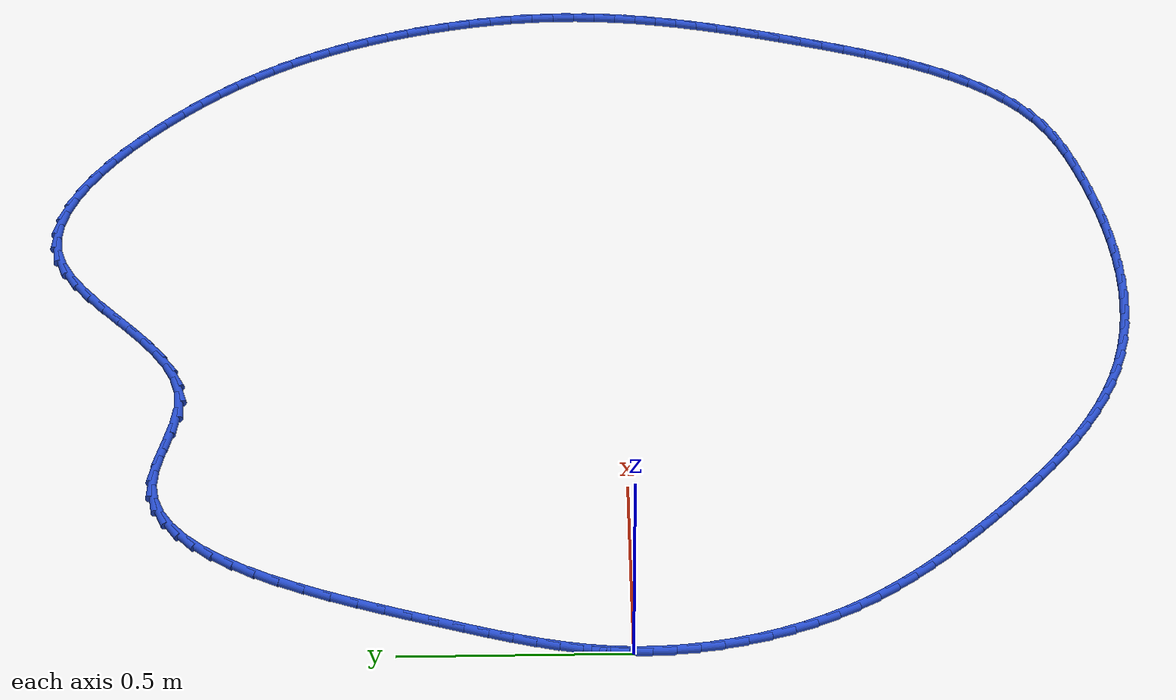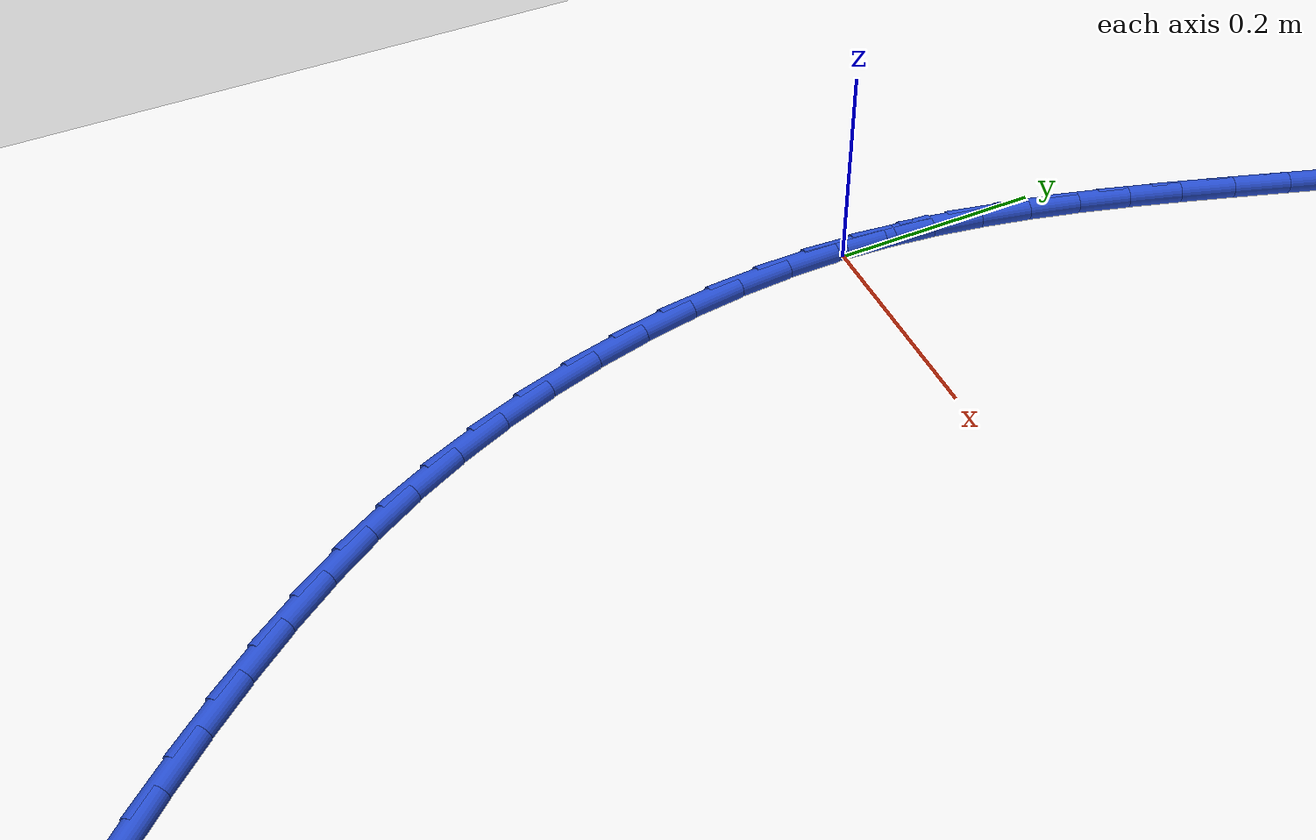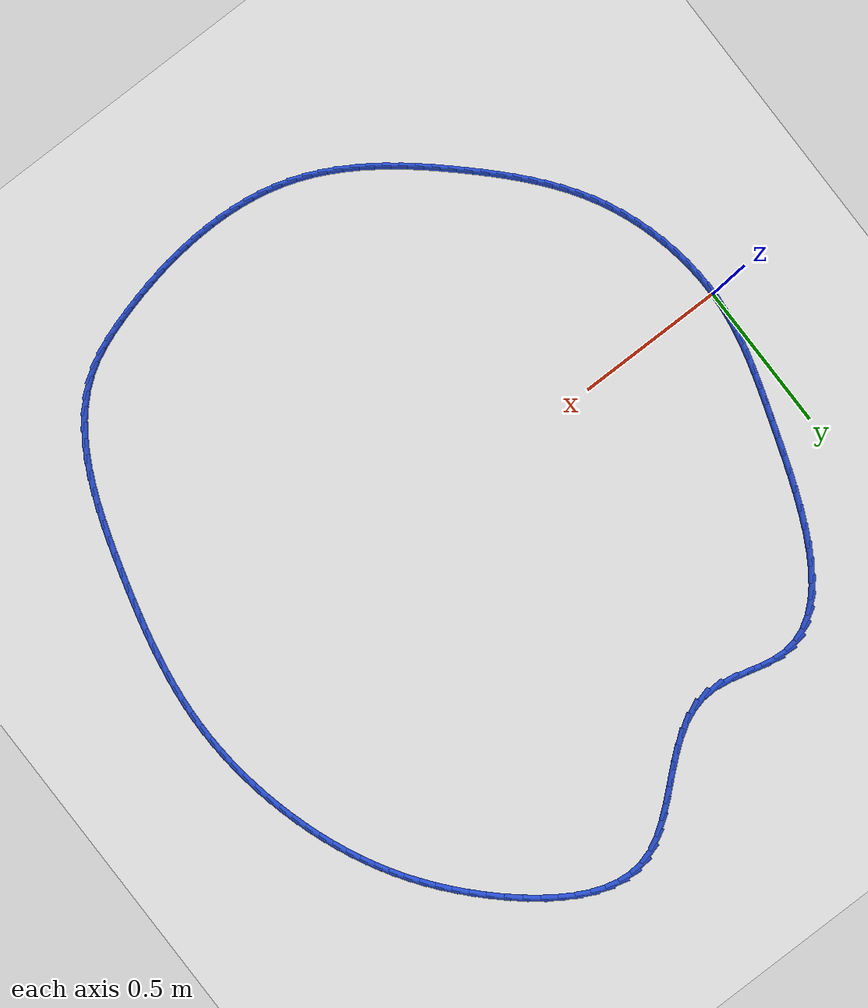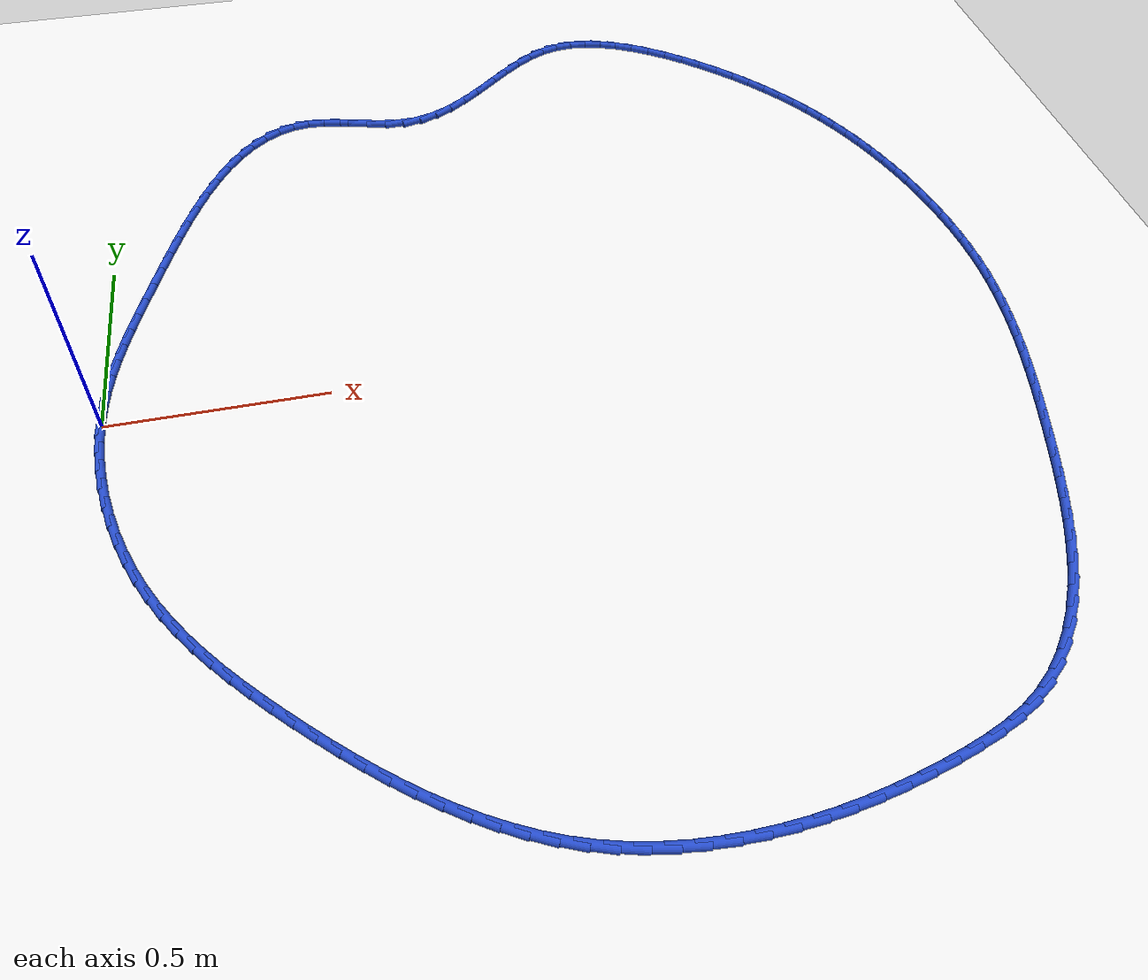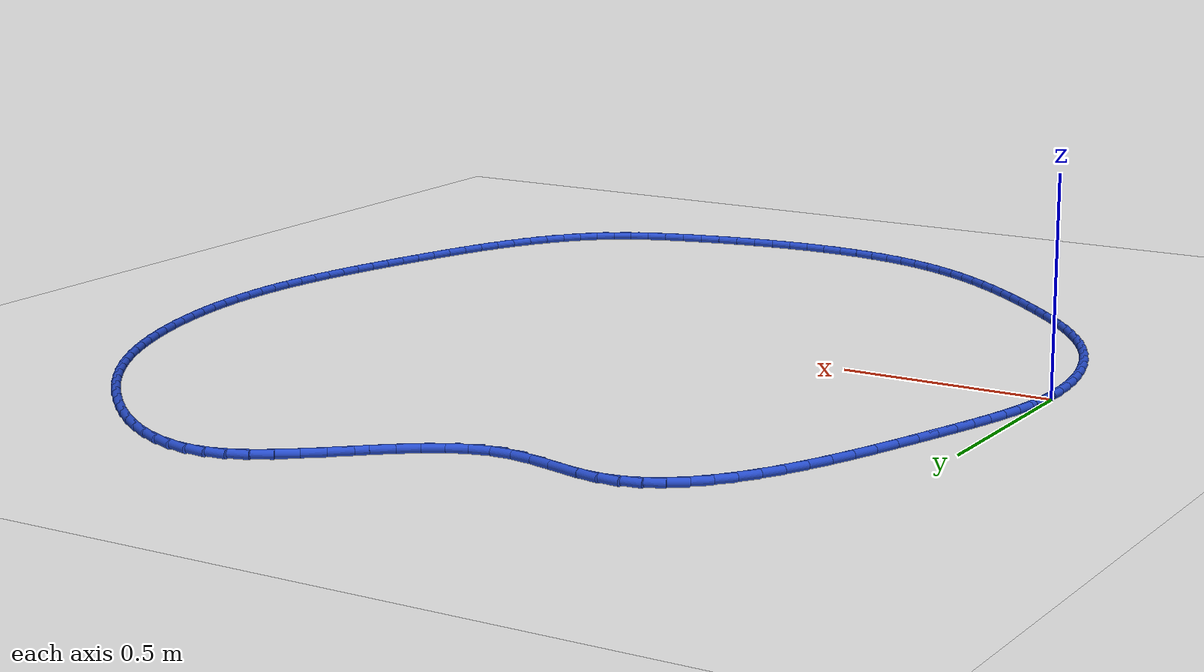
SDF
<sdf version="1.6">
 <world name="default">
  <light name="sun" type="directional">
   <pose>0 0 10 0 -0 0</pose>
   <diffuse>0.8 0.8 0.8 1</diffuse>
   <specular>0.2 0.2 0.2 1</specular>
   <attenuation>
    <range>1000</range>
    <constant>0.9</constant>
    <linear>0.01</linear>
    <quadratic>0.001</quadratic>
   </attenuation>
   <direction>-0.5 0.1 -0.9</direction>
  </light>
  <model name="ground_plane">
   <static>1</static>
   <link name="link">
    <collision name="collision">
     <geometry><plane><normal>0 0 1</normal><size>100 100</size></plane></geometry>
     <surface><friction><ode><mu>100</mu><mu2>50</mu2></ode></friction></surface>
    </collision>
    <visual name="visual">
     <cast_shadows>0</cast_shadows>
     <geometry><plane><normal>0 0 1</normal><size>100 100</size></plane></geometry>
     <material>
      <script><uri>file://media/materials/scripts/gazebo.material</uri><name>Gazebo/WhiteGlow</name></script>
     </material>
    </visual>
   </link>
  </model>
  <gravity>0 0 -9.8</gravity>
  <magnetic_field>6e-06 2.3e-05 -4.2e-05</magnetic_field>
  <atmosphere type="adiabatic"/>
  <physics name="default_physics" default="0" type="ode">
   <max_step_size>0.001</max_step_size>
   <real_time_factor>1</real_time_factor>
   <real_time_update_rate>1000</real_time_update_rate>
  </physics>
  <scene><ambient>0.4 0.4 0.4 1</ambient><background>0.7 0.7 0.7 1</background><shadows>1</shadows></scene>
  <spherical_coordinates>
   <surface_model>EARTH_WGS84</surface_model>
   <latitude_deg>0</latitude_deg>
   <longitude_deg>0</longitude_deg>
   <elevation>0</elevation>
   <heading_deg>0</heading_deg>
  </spherical_coordinates>
  <model name="line">
   <link name="link_0">
    <pose>1.0408340855860843e-17 8.326672684688674e-17 0.01 0 1.57 1.5136941876043444</pose>
    <collision name="collision">
     <geometry><cylinder><radius>0.01</radius><length>0.08</length></cylinder></geometry>
    </collision>
    <visual name="visual">
     <material>
      <script><name>Gazebo/Blue</name><uri>file://media/materials/scripts/gazebo.material</uri></script>
     </material>
     <geometry><cylinder><radius>0.01</radius><length>0.08</length></cylinder></geometry>
    </visual>
   </link>
   <link name="link_1">
    <pose>0.0027870261839059375 0.04875467694186098 0.01 0 1.57 1.455574223660273</pose>
    <collision name="collision">
     <geometry><cylinder><radius>0.01</radius><length>0.08</length></cylinder></geometry>
    </collision>
    <visual name="visual">
     <material>
      <script><name>Gazebo/Blue</name><uri>file://media/materials/scripts/gazebo.material</uri></script>
     </material>
     <geometry><cylinder><radius>0.01</radius><length>0.08</length></cylinder></geometry>
    </visual>
   </link>
   <link name="link_2">
    <pose>0.008354328767920399 0.09685867073324939 0.01 0 1.57 1.403291287682429</pose>
    <collision name="collision">
     <geometry><cylinder><radius>0.01</radius><length>0.08</length></cylinder></geometry>
    </collision>
    <visual name="visual">
     <material>
      <script><name>Gazebo/Blue</name><uri>file://media/materials/scripts/gazebo.material</uri></script>
     </material>
     <geometry><cylinder><radius>0.01</radius><length>0.08</length></cylinder></geometry>
    </visual>
   </link>
   <link name="link_3">
    <pose>0.016441676414029528 0.14468748666733733 0.01 0 1.57 1.358174855953651</pose>
    <collision name="collision">
     <geometry><cylinder><radius>0.01</radius><length>0.08</length></cylinder></geometry>
    </collision>
    <visual name="visual">
     <material>
      <script><name>Gazebo/Blue</name><uri>file://media/materials/scripts/gazebo.material</uri></script>
     </material>
     <geometry><cylinder><radius>0.01</radius><length>0.08</length></cylinder></geometry>
    </visual>
   </link>
   <link name="link_4">
    <pose>0.026788837784219467 0.19261663003729693 0.01 0 1.57 1.3210499428056335</pose>
    <collision name="collision">
     <geometry><cylinder><radius>0.01</radius><length>0.08</length></cylinder></geometry>
    </collision>
    <visual name="visual">
     <material>
      <script><name>Gazebo/Blue</name><uri>file://media/materials/scripts/gazebo.material</uri></script>
     </material>
     <geometry><cylinder><radius>0.01</radius><length>0.08</length></cylinder></geometry>
    </visual>
   </link>
   <link name="link_5">
    <pose>0.03913558154047633 0.24102160613630016 0.01 0 1.57 1.2922552643047283</pose>
    <collision name="collision">
     <geometry><cylinder><radius>0.01</radius><length>0.08</length></cylinder></geometry>
    </collision>
    <visual name="visual">
     <material>
      <script><name>Gazebo/Blue</name><uri>file://media/materials/scripts/gazebo.material</uri></script>
     </material>
     <geometry><cylinder><radius>0.01</radius><length>0.08</length></cylinder></geometry>
    </visual>
   </link>
   <link name="link_6">
    <pose>0.053221676344786285 0.2902779202575192 0.01 0 1.57 1.271719615553586</pose>
    <collision name="collision">
     <geometry><cylinder><radius>0.01</radius><length>0.08</length></cylinder></geometry>
    </collision>
    <visual name="visual">
     <material>
      <script><name>Gazebo/Blue</name><uri>file://media/materials/scripts/gazebo.material</uri></script>
     </material>
     <geometry><cylinder><radius>0.01</radius><length>0.08</length></cylinder></geometry>
    </visual>
   </link>
   <link name="link_7">
    <pose>0.06878689085913542 0.34076107769412595 0.01 0 1.57 1.2590615676463415</pose>
    <collision name="collision">
     <geometry><cylinder><radius>0.01</radius><length>0.08</length></cylinder></geometry>
    </collision>
    <visual name="visual">
     <material>
      <script><name>Gazebo/Blue</name><uri>file://media/materials/scripts/gazebo.material</uri></script>
     </material>
     <geometry><cylinder><radius>0.01</radius><length>0.08</length></cylinder></geometry>
    </visual>
   </link>
   <link name="link_8">
    <pose>0.0855709937455099 0.3928465837392928 0.01 0 1.57 1.2536560702925004</pose>
    <collision name="collision">
     <geometry><cylinder><radius>0.01</radius><length>0.08</length></cylinder></geometry>
    </collision>
    <visual name="visual">
     <material>
      <script><name>Gazebo/Blue</name><uri>file://media/materials/scripts/gazebo.material</uri></script>
     </material>
     <geometry><cylinder><radius>0.01</radius><length>0.08</length></cylinder></geometry>
    </visual>
   </link>
   <link name="link_9">
    <pose>0.10331470347014347 0.4469072296235097 0.01 0 1.57 1.2507052799884115</pose>
    <collision name="collision">
     <geometry><cylinder><radius>0.01</radius><length>0.08</length></cylinder></geometry>
    </collision>
    <visual name="visual">
     <material>
      <script><name>Gazebo/Blue</name><uri>file://media/materials/scripts/gazebo.material</uri></script>
     </material>
     <geometry><cylinder><radius>0.01</radius><length>0.08</length></cylinder></geometry>
    </visual>
   </link>
   <link name="link_10">
    <pose>0.12188962666116884 0.5029417940619865 0.01 0 1.57 1.2418944668132033</pose>
    <collision name="collision">
     <geometry><cylinder><radius>0.01</radius><length>0.08</length></cylinder></geometry>
    </collision>
    <visual name="visual">
     <material>
      <script><name>Gazebo/Blue</name><uri>file://media/materials/scripts/gazebo.material</uri></script>
     </material>
     <geometry><cylinder><radius>0.01</radius><length>0.08</length></cylinder></geometry>
    </visual>
   </link>
   <link name="link_11">
    <pose>0.14143064655290796 0.5601967436871068 0.01 0 1.57 1.2263753570486027</pose>
    <collision name="collision">
     <geometry><cylinder><radius>0.01</radius><length>0.08</length></cylinder></geometry>
    </collision>
    <visual name="visual">
     <material>
      <script><name>Gazebo/Blue</name><uri>file://media/materials/scripts/gazebo.material</uri></script>
     </material>
     <geometry><cylinder><radius>0.01</radius><length>0.08</length></cylinder></geometry>
    </visual>
   </link>
   <link name="link_12">
    <pose>0.16210420102167475 0.6178283778399654 0.01 0 1.57 1.2038337937438826</pose>
    <collision name="collision">
     <geometry><cylinder><radius>0.01</radius><length>0.08</length></cylinder></geometry>
    </collision>
    <visual name="visual">
     <material>
      <script><name>Gazebo/Blue</name><uri>file://media/materials/scripts/gazebo.material</uri></script>
     </material>
     <geometry><cylinder><radius>0.01</radius><length>0.08</length></cylinder></geometry>
    </visual>
   </link>
   <link name="link_13">
    <pose>0.18407672794378316 0.6749929958616567 0.01 0 1.57 1.1734834334014868</pose>
    <collision name="collision">
     <geometry><cylinder><radius>0.01</radius><length>0.08</length></cylinder></geometry>
    </collision>
    <visual name="visual">
     <material>
      <script><name>Gazebo/Blue</name><uri>file://media/materials/scripts/gazebo.material</uri></script>
     </material>
     <geometry><cylinder><radius>0.01</radius><length>0.08</length></cylinder></geometry>
    </visual>
   </link>
   <link name="link_14">
    <pose>0.20751466519554707 0.7308468970932753 0.01 0 1.57 1.1340158557307733</pose>
    <collision name="collision">
     <geometry><cylinder><radius>0.01</radius><length>0.08</length></cylinder></geometry>
    </collision>
    <visual name="visual">
     <material>
      <script><name>Gazebo/Blue</name><uri>file://media/materials/scripts/gazebo.material</uri></script>
     </material>
     <geometry><cylinder><radius>0.01</radius><length>0.08</length></cylinder></geometry>
    </visual>
   </link>
   <link name="link_15">
    <pose>0.23258445065328057 0.7845463808759163 0.01 0 1.57 1.0834939866862894</pose>
    <collision name="collision">
     <geometry><cylinder><radius>0.01</radius><length>0.08</length></cylinder></geometry>
    </collision>
    <visual name="visual">
     <material>
      <script><name>Gazebo/Blue</name><uri>file://media/materials/scripts/gazebo.material</uri></script>
     </material>
     <geometry><cylinder><radius>0.01</radius><length>0.08</length></cylinder></geometry>
    </visual>
   </link>
   <link name="link_16">
    <pose>0.2594525221932976 0.8352477465506742 0.01 0 1.57 1.0192009198900167</pose>
    <collision name="collision">
     <geometry><cylinder><radius>0.01</radius><length>0.08</length></cylinder></geometry>
    </collision>
    <visual name="visual">
     <material>
      <script><name>Gazebo/Blue</name><uri>file://media/materials/scripts/gazebo.material</uri></script>
     </material>
     <geometry><cylinder><radius>0.01</radius><length>0.08</length></cylinder></geometry>
    </visual>
   </link>
   <link name="link_17">
    <pose>0.2882853176919122 0.8821072934586434 0.01 0 1.57 0.937487432368117</pose>
    <collision name="collision">
     <geometry><cylinder><radius>0.01</radius><length>0.08</length></cylinder></geometry>
    </collision>
    <visual name="visual">
     <material>
      <script><name>Gazebo/Blue</name><uri>file://media/materials/scripts/gazebo.material</uri></script>
     </material>
     <geometry><cylinder><radius>0.01</radius><length>0.08</length></cylinder></geometry>
    </visual>
   </link>
   <link name="link_18">
    <pose>0.319249275025438 0.9242813209409185 0.01 0 1.57 0.8337573164377134</pose>
    <collision name="collision">
     <geometry><cylinder><radius>0.01</radius><length>0.08</length></cylinder></geometry>
    </collision>
    <visual name="visual">
     <material>
      <script><name>Gazebo/Blue</name><uri>file://media/materials/scripts/gazebo.material</uri></script>
     </material>
     <geometry><cylinder><radius>0.01</radius><length>0.08</length></cylinder></geometry>
    </visual>
   </link>
   <link name="link_19">
    <pose>0.35251083207018935 0.9609261283385949 0.01 0 1.57 0.7029503967403277</pose>
    <collision name="collision">
     <geometry><cylinder><radius>0.01</radius><length>0.08</length></cylinder></geometry>
    </collision>
    <visual name="visual">
     <material>
      <script><name>Gazebo/Blue</name><uri>file://media/materials/scripts/gazebo.material</uri></script>
     </material>
     <geometry><cylinder><radius>0.01</radius><length>0.08</length></cylinder></geometry>
    </visual>
   </link>
   <link name="link_20">
    <pose>0.38823642670247993 0.9911980149927662 0.01 0 1.57 0.5412170438605266</pose>
    <collision name="collision">
     <geometry><cylinder><radius>0.01</radius><length>0.08</length></cylinder></geometry>
    </collision>
    <visual name="visual">
     <material>
      <script><name>Gazebo/Blue</name><uri>file://media/materials/scripts/gazebo.material</uri></script>
     </material>
     <geometry><cylinder><radius>0.01</radius><length>0.08</length></cylinder></geometry>
    </visual>
   </link>
   <link name="link_21">
    <pose>0.42659249679862393 1.0142532802445279 0.01 0 1.57 0.34941946381717975</pose>
    <collision name="collision">
     <geometry><cylinder><radius>0.01</radius><length>0.08</length></cylinder></geometry>
    </collision>
    <visual name="visual">
     <material>
      <script><name>Gazebo/Blue</name><uri>file://media/materials/scripts/gazebo.material</uri></script>
     </material>
     <geometry><cylinder><radius>0.01</radius><length>0.08</length></cylinder></geometry>
    </visual>
   </link>
   <link name="link_22">
    <pose>0.4677454802349351 1.029248223434974 0.01 0 1.57 0.1371976080069714</pose>
    <collision name="collision">
     <geometry><cylinder><radius>0.01</radius><length>0.08</length></cylinder></geometry>
    </collision>
    <visual name="visual">
     <material>
      <script><name>Gazebo/Blue</name><uri>file://media/materials/scripts/gazebo.material</uri></script>
     </material>
     <geometry><cylinder><radius>0.01</radius><length>0.08</length></cylinder></geometry>
    </visual>
   </link>
   <link name="link_23">
    <pose>0.5118618148877275 1.0353391439051995 0.01 0 1.57 -0.07048215105526898</pose>
    <collision name="collision">
     <geometry><cylinder><radius>0.01</radius><length>0.08</length></cylinder></geometry>
    </collision>
    <visual name="visual">
     <material>
      <script><name>Gazebo/Blue</name><uri>file://media/materials/scripts/gazebo.material</uri></script>
     </material>
     <geometry><cylinder><radius>0.01</radius><length>0.08</length></cylinder></geometry>
    </visual>
   </link>
   <link name="link_24">
    <pose>0.5590275122081958 1.0320092883298853 0.01 0 1.57 -0.20474373316825215</pose>
    <collision name="collision">
     <geometry><cylinder><radius>0.01</radius><length>0.08</length></cylinder></geometry>
    </collision>
    <visual name="visual">
     <material>
      <script><name>Gazebo/Blue</name><uri>file://media/materials/scripts/gazebo.material</uri></script>
     </material>
     <geometry><cylinder><radius>0.01</radius><length>0.08</length></cylinder></geometry>
    </visual>
   </link>
   <link name="link_25">
    <pose>0.6085969756556932 1.0217160164542238 0.01 0 1.57 -0.25378165518661827</pose>
    <collision name="collision">
     <geometry><cylinder><radius>0.01</radius><length>0.08</length></cylinder></geometry>
    </collision>
    <visual name="visual">
     <material>
      <script><name>Gazebo/Blue</name><uri>file://media/materials/scripts/gazebo.material</uri></script>
     </material>
     <geometry><cylinder><radius>0.01</radius><length>0.08</length></cylinder></geometry>
    </visual>
   </link>
   <link name="link_26">
    <pose>0.6595340803596135 1.008504253254374 0.01 0 1.57 -0.23124023984671754</pose>
    <collision name="collision">
     <geometry><cylinder><radius>0.01</radius><length>0.08</length></cylinder></geometry>
    </collision>
    <visual name="visual">
     <material>
      <script><name>Gazebo/Blue</name><uri>file://media/materials/scripts/gazebo.material</uri></script>
     </material>
     <geometry><cylinder><radius>0.01</radius><length>0.08</length></cylinder></geometry>
    </visual>
   </link>
   <link name="link_27">
    <pose>0.7107990376394291 0.9964338177277346 0.01 0 1.57 -0.13505567940816368</pose>
    <collision name="collision">
     <geometry><cylinder><radius>0.01</radius><length>0.08</length></cylinder></geometry>
    </collision>
    <visual name="visual">
     <material>
      <script><name>Gazebo/Blue</name><uri>file://media/materials/scripts/gazebo.material</uri></script>
     </material>
     <geometry><cylinder><radius>0.01</radius><length>0.08</length></cylinder></geometry>
    </visual>
   </link>
   <link name="link_28">
    <pose>0.7613520588146127 0.9895645288717068 0.01 0 1.57 0.046825465814953546</pose>
    <collision name="collision">
     <geometry><cylinder><radius>0.01</radius><length>0.08</length></cylinder></geometry>
    </collision>
    <visual name="visual">
     <material>
      <script><name>Gazebo/Blue</name><uri>file://media/materials/scripts/gazebo.material</uri></script>
     </material>
     <geometry><cylinder><radius>0.01</radius><length>0.08</length></cylinder></geometry>
    </visual>
   </link>
   <link name="link_29">
    <pose>0.8101775216296122 0.9918524763591821 0.01 0 1.57 0.26447070230103303</pose>
    <collision name="collision">
     <geometry><cylinder><radius>0.01</radius><length>0.08</length></cylinder></geometry>
    </collision>
    <visual name="visual">
     <material>
      <script><name>Gazebo/Blue</name><uri>file://media/materials/scripts/gazebo.material</uri></script>
     </material>
     <geometry><cylinder><radius>0.01</radius><length>0.08</length></cylinder></geometry>
    </visual>
   </link>
   <link name="link_30">
    <pose>0.8569000542258998 1.00450560894977 0.01 0 1.57 0.44192383713737715</pose>
    <collision name="collision">
     <geometry><cylinder><radius>0.01</radius><length>0.08</length></cylinder></geometry>
    </collision>
    <visual name="visual">
     <material>
      <script><name>Gazebo/Blue</name><uri>file://media/materials/scripts/gazebo.material</uri></script>
     </material>
     <geometry><cylinder><radius>0.01</radius><length>0.08</length></cylinder></geometry>
    </visual>
   </link>
   <link name="link_31">
    <pose>0.9018352759688302 1.0257659401035617 0.01 0 1.57 0.5713254970687769</pose>
    <collision name="collision">
     <geometry><cylinder><radius>0.01</radius><length>0.08</length></cylinder></geometry>
    </collision>
    <visual name="visual">
     <material>
      <script><name>Gazebo/Blue</name><uri>file://media/materials/scripts/gazebo.material</uri></script>
     </material>
     <geometry><cylinder><radius>0.01</radius><length>0.08</length></cylinder></geometry>
    </visual>
   </link>
   <link name="link_32">
    <pose>0.9453331393223067 1.0537281156363023 0.01 0 1.57 0.6576958909121613</pose>
    <collision name="collision">
     <geometry><cylinder><radius>0.01</radius><length>0.08</length></cylinder></geometry>
    </collision>
    <visual name="visual">
     <material>
      <script><name>Gazebo/Blue</name><uri>file://media/materials/scripts/gazebo.material</uri></script>
     </material>
     <geometry><cylinder><radius>0.01</radius><length>0.08</length></cylinder></geometry>
    </visual>
   </link>
   <link name="link_33">
    <pose>0.9877435967502327 1.0864867813637376 0.01 0 1.57 0.7076583093968649</pose>
    <collision name="collision">
     <geometry><cylinder><radius>0.01</radius><length>0.08</length></cylinder></geometry>
    </collision>
    <visual name="visual">
     <material>
      <script><name>Gazebo/Blue</name><uri>file://media/materials/scripts/gazebo.material</uri></script>
     </material>
     <geometry><cylinder><radius>0.01</radius><length>0.08</length></cylinder></geometry>
    </visual>
   </link>
   <link name="link_34">
    <pose>1.0294166007165115 1.1221365831016124 0.01 0 1.57 0.7257941228557021</pose>
    <collision name="collision">
     <geometry><cylinder><radius>0.01</radius><length>0.08</length></cylinder></geometry>
    </collision>
    <visual name="visual">
     <material>
      <script><name>Gazebo/Blue</name><uri>file://media/materials/scripts/gazebo.material</uri></script>
     </material>
     <geometry><cylinder><radius>0.01</radius><length>0.08</length></cylinder></geometry>
    </visual>
   </link>
   <link name="link_35">
    <pose>1.0707021036850466 1.1587721666656723 0.01 0 1.57 0.7136445053751762</pose>
    <collision name="collision">
     <geometry><cylinder><radius>0.01</radius><length>0.08</length></cylinder></geometry>
    </collision>
    <visual name="visual">
     <material>
      <script><name>Gazebo/Blue</name><uri>file://media/materials/scripts/gazebo.material</uri></script>
     </material>
     <geometry><cylinder><radius>0.01</radius><length>0.08</length></cylinder></geometry>
    </visual>
   </link>
   <link name="link_36">
    <pose>1.111950058119741 1.194488177871663 0.01 0 1.57 0.6694782082863653</pose>
    <collision name="collision">
     <geometry><cylinder><radius>0.01</radius><length>0.08</length></cylinder></geometry>
    </collision>
    <visual name="visual">
     <material>
      <script><name>Gazebo/Blue</name><uri>file://media/materials/scripts/gazebo.material</uri></script>
     </material>
     <geometry><cylinder><radius>0.01</radius><length>0.08</length></cylinder></geometry>
    </visual>
   </link>
   <link name="link_37">
    <pose>1.1535104164844983 1.2273792625353295 0.01 0 1.57 0.5882047038995217</pose>
    <collision name="collision">
     <geometry><cylinder><radius>0.01</radius><length>0.08</length></cylinder></geometry>
    </collision>
    <visual name="visual">
     <material>
      <script><name>Gazebo/Blue</name><uri>file://media/materials/scripts/gazebo.material</uri></script>
     </material>
     <geometry><cylinder><radius>0.01</radius><length>0.08</length></cylinder></geometry>
    </visual>
   </link>
   <link name="link_38">
    <pose>1.1957331312432213 1.2555400664724172 0.01 0 1.57 0.4619374834004188</pose>
    <collision name="collision">
     <geometry><cylinder><radius>0.01</radius><length>0.08</length></cylinder></geometry>
    </collision>
    <visual name="visual">
     <material>
      <script><name>Gazebo/Blue</name><uri>file://media/materials/scripts/gazebo.material</uri></script>
     </material>
     <geometry><cylinder><radius>0.01</radius><length>0.08</length></cylinder></geometry>
    </visual>
   </link>
   <link name="link_39">
    <pose>1.2389681548598137 1.2770652354986713 0.01 0 1.57 0.2837549110535024</pose>
    <collision name="collision">
     <geometry><cylinder><radius>0.01</radius><length>0.08</length></cylinder></geometry>
    </collision>
    <visual name="visual">
     <material>
      <script><name>Gazebo/Blue</name><uri>file://media/materials/scripts/gazebo.material</uri></script>
     </material>
     <geometry><cylinder><radius>0.01</radius><length>0.08</length></cylinder></geometry>
    </visual>
   </link>
   <link name="link_40">
    <pose>1.2835600741356075 1.2900693153601732 0.01 0 1.57 0.07974830350344746</pose>
    <collision name="collision">
     <geometry><cylinder><radius>0.01</radius><length>0.08</length></cylinder></geometry>
    </collision>
    <visual name="visual">
     <material>
      <script><name>Gazebo/Blue</name><uri>file://media/materials/scripts/gazebo.material</uri></script>
     </material>
     <geometry><cylinder><radius>0.01</radius><length>0.08</length></cylinder></geometry>
    </visual>
   </link>
   <link name="link_41">
    <pose>1.3295625745194417 1.2937457337811922 0.01 0 1.57 -0.10272631332635304</pose>
    <collision name="collision">
     <geometry><cylinder><radius>0.01</radius><length>0.08</length></cylinder></geometry>
    </collision>
    <visual name="visual">
     <material>
      <script><name>Gazebo/Blue</name><uri>file://media/materials/scripts/gazebo.material</uri></script>
     </material>
     <geometry><cylinder><radius>0.01</radius><length>0.08</length></cylinder></geometry>
    </visual>
   </link>
   <link name="link_42">
    <pose>1.3765954397768552 1.2888971537212535 0.01 0 1.57 -0.2553747519276079</pose>
    <collision name="collision">
     <geometry><cylinder><radius>0.01</radius><length>0.08</length></cylinder></geometry>
    </collision>
    <visual name="visual">
     <material>
      <script><name>Gazebo/Blue</name><uri>file://media/materials/scripts/gazebo.material</uri></script>
     </material>
     <geometry><cylinder><radius>0.01</radius><length>0.08</length></cylinder></geometry>
    </visual>
   </link>
   <link name="link_43">
    <pose>1.4242430468497547 1.276457553390212 0.01 0 1.57 -0.3797485571304839</pose>
    <collision name="collision">
     <geometry><cylinder><radius>0.01</radius><length>0.08</length></cylinder></geometry>
    </collision>
    <visual name="visual">
     <material>
      <script><name>Gazebo/Blue</name><uri>file://media/materials/scripts/gazebo.material</uri></script>
     </material>
     <geometry><cylinder><radius>0.01</radius><length>0.08</length></cylinder></geometry>
    </visual>
   </link>
   <link name="link_44">
    <pose>1.472089772680048 1.2573609109979225 0.01 0 1.57 -0.48037813025264886</pose>
    <collision name="collision">
     <geometry><cylinder><radius>0.01</radius><length>0.08</length></cylinder></geometry>
    </collision>
    <visual name="visual">
     <material>
      <script><name>Gazebo/Blue</name><uri>file://media/materials/scripts/gazebo.material</uri></script>
     </material>
     <geometry><cylinder><radius>0.01</radius><length>0.08</length></cylinder></geometry>
    </visual>
   </link>
   <link name="link_45">
    <pose>1.5197199942096387 1.2325412047542388 0.01 0 1.57 -0.5621866305383663</pose>
    <collision name="collision">
     <geometry><cylinder><radius>0.01</radius><length>0.08</length></cylinder></geometry>
    </collision>
    <visual name="visual">
     <material>
      <script><name>Gazebo/Blue</name><uri>file://media/materials/scripts/gazebo.material</uri></script>
     </material>
     <geometry><cylinder><radius>0.01</radius><length>0.08</length></cylinder></geometry>
    </visual>
   </link>
   <link name="link_46">
    <pose>1.5667180883804355 1.202932412869015 0.01 0 1.57 -0.6294431630855104</pose>
    <collision name="collision">
     <geometry><cylinder><radius>0.01</radius><length>0.08</length></cylinder></geometry>
    </collision>
    <visual name="visual">
     <material>
      <script><name>Gazebo/Blue</name><uri>file://media/materials/scripts/gazebo.material</uri></script>
     </material>
     <geometry><cylinder><radius>0.01</radius><length>0.08</length></cylinder></geometry>
    </visual>
   </link>
   <link name="link_47">
    <pose>1.612668432134342 1.1694685135521061 0.01 0 1.57 -0.6855490326683987</pose>
    <collision name="collision">
     <geometry><cylinder><radius>0.01</radius><length>0.08</length></cylinder></geometry>
    </collision>
    <visual name="visual">
     <material>
      <script><name>Gazebo/Blue</name><uri>file://media/materials/scripts/gazebo.material</uri></script>
     </material>
     <geometry><cylinder><radius>0.01</radius><length>0.08</length></cylinder></geometry>
    </visual>
   </link>
   <link name="link_48">
    <pose>1.6571554024132664 1.1330834850133662 0.01 0 1.57 -0.7331392167358219</pose>
    <collision name="collision">
     <geometry><cylinder><radius>0.01</radius><length>0.08</length></cylinder></geometry>
    </collision>
    <visual name="visual">
     <material>
      <script><name>Gazebo/Blue</name><uri>file://media/materials/scripts/gazebo.material</uri></script>
     </material>
     <geometry><cylinder><radius>0.01</radius><length>0.08</length></cylinder></geometry>
    </visual>
   </link>
   <link name="link_49">
    <pose>1.699763376159114 1.0947113054626496 0.01 0 1.57 -0.7742659379264477</pose>
    <collision name="collision">
     <geometry><cylinder><radius>0.01</radius><length>0.08</length></cylinder></geometry>
    </collision>
    <visual name="visual">
     <material>
      <script><name>Gazebo/Blue</name><uri>file://media/materials/scripts/gazebo.material</uri></script>
     </material>
     <geometry><cylinder><radius>0.01</radius><length>0.08</length></cylinder></geometry>
    </visual>
   </link>
   <link name="link_50">
    <pose>1.7400770391479747 1.0552853584619604 0.01 0 1.57 -0.8120348778406468</pose>
    <collision name="collision">
     <geometry><cylinder><radius>0.01</radius><length>0.08</length></cylinder></geometry>
    </collision>
    <visual name="visual">
     <material>
      <script><name>Gazebo/Blue</name><uri>file://media/materials/scripts/gazebo.material</uri></script>
     </material>
     <geometry><cylinder><radius>0.01</radius><length>0.08</length></cylinder></geometry>
    </visual>
   </link>
   <link name="link_51">
    <pose>1.777814674057478 1.0154817920904236 0.01 0 1.57 -0.8508529733878075</pose>
    <collision name="collision">
     <geometry><cylinder><radius>0.01</radius><length>0.08</length></cylinder></geometry>
    </collision>
    <visual name="visual">
     <material>
      <script><name>Gazebo/Blue</name><uri>file://media/materials/scripts/gazebo.material</uri></script>
     </material>
     <geometry><cylinder><radius>0.01</radius><length>0.08</length></cylinder></geometry>
    </visual>
   </link>
   <link name="link_52">
    <pose>1.813036212894146 0.9753189223286682 0.01 0 1.57 -0.8910721220932384</pose>
    <collision name="collision">
     <geometry><cylinder><radius>0.01</radius><length>0.08</length></cylinder></geometry>
    </collision>
    <visual name="visual">
     <material>
      <script><name>Gazebo/Blue</name><uri>file://media/materials/scripts/gazebo.material</uri></script>
     </material>
     <geometry><cylinder><radius>0.01</radius><length>0.08</length></cylinder></geometry>
    </visual>
   </link>
   <link name="link_53">
    <pose>1.8458554231601072 0.9347114070668334 0.01 0 1.57 -0.9323311009404979</pose>
    <collision name="collision">
     <geometry><cylinder><radius>0.01</radius><length>0.08</length></cylinder></geometry>
    </collision>
    <visual name="visual">
     <material>
      <script><name>Gazebo/Blue</name><uri>file://media/materials/scripts/gazebo.material</uri></script>
     </material>
     <geometry><cylinder><radius>0.01</radius><length>0.08</length></cylinder></geometry>
    </visual>
   </link>
   <link name="link_54">
    <pose>1.876386072357492 0.8935739041950591 0.01 0 1.57 -0.9742106515285777</pose>
    <collision name="collision">
     <geometry><cylinder><radius>0.01</radius><length>0.08</length></cylinder></geometry>
    </collision>
    <visual name="visual">
     <material>
      <script><name>Gazebo/Blue</name><uri>file://media/materials/scripts/gazebo.material</uri></script>
     </material>
     <geometry><cylinder><radius>0.01</radius><length>0.08</length></cylinder></geometry>
    </visual>
   </link>
   <link name="link_55">
    <pose>1.9047419279884314 0.8518210716034837 0.01 0 1.57 -1.0162489458181112</pose>
    <collision name="collision">
     <geometry><cylinder><radius>0.01</radius><length>0.08</length></cylinder></geometry>
    </collision>
    <visual name="visual">
     <material>
      <script><name>Gazebo/Blue</name><uri>file://media/materials/scripts/gazebo.material</uri></script>
     </material>
     <geometry><cylinder><radius>0.01</radius><length>0.08</length></cylinder></geometry>
    </visual>
   </link>
   <link name="link_56">
    <pose>1.9310367575550542 0.8093675671822474 0.01 0 1.57 -1.0579617639497414</pose>
    <collision name="collision">
     <geometry><cylinder><radius>0.01</radius><length>0.08</length></cylinder></geometry>
    </collision>
    <visual name="visual">
     <material>
      <script><name>Gazebo/Blue</name><uri>file://media/materials/scripts/gazebo.material</uri></script>
     </material>
     <geometry><cylinder><radius>0.01</radius><length>0.08</length></cylinder></geometry>
    </visual>
   </link>
   <link name="link_57">
    <pose>1.9553843285594916 0.7661280488214893 0.01 0 1.57 -1.098865359921488</pose>
    <collision name="collision">
     <geometry><cylinder><radius>0.01</radius><length>0.08</length></cylinder></geometry>
    </collision>
    <visual name="visual">
     <material>
      <script><name>Gazebo/Blue</name><uri>file://media/materials/scripts/gazebo.material</uri></script>
     </material>
     <geometry><cylinder><radius>0.01</radius><length>0.08</length></cylinder></geometry>
    </visual>
   </link>
   <link name="link_58">
    <pose>1.977898408503872 0.7220171744113488 0.01 0 1.57 -1.1384994398374577</pose>
    <collision name="collision">
     <geometry><cylinder><radius>0.01</radius><length>0.08</length></cylinder></geometry>
    </collision>
    <visual name="visual">
     <material>
      <script><name>Gazebo/Blue</name><uri>file://media/materials/scripts/gazebo.material</uri></script>
     </material>
     <geometry><cylinder><radius>0.01</radius><length>0.08</length></cylinder></geometry>
    </visual>
   </link>
   <link name="link_59">
    <pose>1.9986927648903263 0.6769496018419651 0.01 0 1.57 -1.1764476515463638</pose>
    <collision name="collision">
     <geometry><cylinder><radius>0.01</radius><length>0.08</length></cylinder></geometry>
    </collision>
    <visual name="visual">
     <material>
      <script><name>Gazebo/Blue</name><uri>file://media/materials/scripts/gazebo.material</uri></script>
     </material>
     <geometry><cylinder><radius>0.01</radius><length>0.08</length></cylinder></geometry>
    </visual>
   </link>
   <link name="link_60">
    <pose>2.017881165199985 0.6308399890321844 0.01 0 1.57 -1.212616297254871</pose>
    <collision name="collision">
     <geometry><cylinder><radius>0.01</radius><length>0.08</length></cylinder></geometry>
    </collision>
    <visual name="visual">
     <material>
      <script><name>Gazebo/Blue</name><uri>file://media/materials/scripts/gazebo.material</uri></script>
     </material>
     <geometry><cylinder><radius>0.01</radius><length>0.08</length></cylinder></geometry>
    </visual>
   </link>
   <link name="link_61">
    <pose>2.0355483888272343 0.583642619864845 0.01 0 1.57 -1.2479417275420543</pose>
    <collision name="collision">
     <geometry><cylinder><radius>0.01</radius><length>0.08</length></cylinder></geometry>
    </collision>
    <visual name="visual">
     <material>
      <script><name>Gazebo/Blue</name><uri>file://media/materials/scripts/gazebo.material</uri></script>
     </material>
     <geometry><cylinder><radius>0.01</radius><length>0.08</length></cylinder></geometry>
    </visual>
   </link>
   <link name="link_62">
    <pose>2.0516663725087176 0.5354660312141015 0.01 0 1.57 -1.2828942968265042</pose>
    <collision name="collision">
     <geometry><cylinder><radius>0.01</radius><length>0.08</length></cylinder></geometry>
    </collision>
    <visual name="visual">
     <material>
      <script><name>Gazebo/Blue</name><uri>file://media/materials/scripts/gazebo.material</uri></script>
     </material>
     <geometry><cylinder><radius>0.01</radius><length>0.08</length></cylinder></geometry>
    </visual>
   </link>
   <link name="link_63">
    <pose>2.0661795989995793 0.4864562888359562 0.01 0 1.57 -1.3177145729441209</pose>
    <collision name="collision">
     <geometry><cylinder><radius>0.01</radius><length>0.08</length></cylinder></geometry>
    </collision>
    <visual name="visual">
     <material>
      <script><name>Gazebo/Blue</name><uri>file://media/materials/scripts/gazebo.material</uri></script>
     </material>
     <geometry><cylinder><radius>0.01</radius><length>0.08</length></cylinder></geometry>
    </visual>
   </link>
   <link name="link_64">
    <pose>2.079032551054962 0.43675945848641207 0.01 0 1.57 -1.352635926681079</pose>
    <collision name="collision">
     <geometry><cylinder><radius>0.01</radius><length>0.08</length></cylinder></geometry>
    </collision>
    <visual name="visual">
     <material>
      <script><name>Gazebo/Blue</name><uri>file://media/materials/scripts/gazebo.material</uri></script>
     </material>
     <geometry><cylinder><radius>0.01</radius><length>0.08</length></cylinder></geometry>
    </visual>
   </link>
   <link name="link_65">
    <pose>2.0901697114300095 0.38652160592147156 0.01 0 1.57 -1.3878878243471289</pose>
    <collision name="collision">
     <geometry><cylinder><radius>0.01</radius><length>0.08</length></cylinder></geometry>
    </collision>
    <visual name="visual">
     <material>
      <script><name>Gazebo/Blue</name><uri>file://media/materials/scripts/gazebo.material</uri></script>
     </material>
     <geometry><cylinder><radius>0.01</radius><length>0.08</length></cylinder></geometry>
    </visual>
   </link>
   <link name="link_66">
    <pose>2.0995355628798653 0.33588879689713674 0.01 0 1.57 -1.4236988229936416</pose>
    <collision name="collision">
     <geometry><cylinder><radius>0.01</radius><length>0.08</length></cylinder></geometry>
    </collision>
    <visual name="visual">
     <material>
      <script><name>Gazebo/Blue</name><uri>file://media/materials/scripts/gazebo.material</uri></script>
     </material>
     <geometry><cylinder><radius>0.01</radius><length>0.08</length></cylinder></geometry>
    </visual>
   </link>
   <link name="link_67">
    <pose>2.1070745881596724 0.28500709716941114 0.01 0 1.57 -1.4602992457787685</pose>
    <collision name="collision">
     <geometry><cylinder><radius>0.01</radius><length>0.08</length></cylinder></geometry>
    </collision>
    <visual name="visual">
     <material>
      <script><name>Gazebo/Blue</name><uri>file://media/materials/scripts/gazebo.material</uri></script>
     </material>
     <geometry><cylinder><radius>0.01</radius><length>0.08</length></cylinder></geometry>
    </visual>
   </link>
   <link name="link_68">
    <pose>2.1127312700245753 0.2340225724942966 0.01 0 1.57 -1.4979234873334326</pose>
    <collision name="collision">
     <geometry><cylinder><radius>0.01</radius><length>0.08</length></cylinder></geometry>
    </collision>
    <visual name="visual">
     <material>
      <script><name>Gazebo/Blue</name><uri>file://media/materials/scripts/gazebo.material</uri></script>
     </material>
     <geometry><cylinder><radius>0.01</radius><length>0.08</length></cylinder></geometry>
    </visual>
   </link>
   <link name="link_69">
    <pose>2.116450091229716 0.18308128862779643 0.01 0 1.57 -1.5368118580601426</pose>
    <collision name="collision">
     <geometry><cylinder><radius>0.01</radius><length>0.08</length></cylinder></geometry>
    </collision>
    <visual name="visual">
     <material>
      <script><name>Gazebo/Blue</name><uri>file://media/materials/scripts/gazebo.material</uri></script>
     </material>
     <geometry><cylinder><radius>0.01</radius><length>0.08</length></cylinder></geometry>
    </visual>
   </link>
   <link name="link_70">
    <pose>2.118175534530239 0.1323293113259126 0.01 0 1.57 1.564454005626136</pose>
    <collision name="collision">
     <geometry><cylinder><radius>0.01</radius><length>0.08</length></cylinder></geometry>
    </collision>
    <visual name="visual">
     <material>
      <script><name>Gazebo/Blue</name><uri>file://media/materials/scripts/gazebo.material</uri></script>
     </material>
     <geometry><cylinder><radius>0.01</radius><length>0.08</length></cylinder></geometry>
    </visual>
   </link>
   <link name="link_71">
    <pose>2.1178557430893012 0.08190815721797923 0.01 0 1.57 1.5243360530999805</pose>
    <collision name="collision">
     <geometry><cylinder><radius>0.01</radius><length>0.08</length></cylinder></geometry>
    </collision>
    <visual name="visual">
     <material>
      <script><name>Gazebo/Blue</name><uri>file://media/materials/scripts/gazebo.material</uri></script>
     </material>
     <geometry><cylinder><radius>0.01</radius><length>0.08</length></cylinder></geometry>
    </visual>
   </link>
   <link name="link_72">
    <pose>2.1155282700317573 0.031848224926894285 0.01 0 1.57 1.48652621558645</pose>
    <collision name="collision">
     <geometry><cylinder><radius>0.01</radius><length>0.08</length></cylinder></geometry>
    </collision>
    <visual name="visual">
     <material>
      <script><name>Gazebo/Blue</name><uri>file://media/materials/scripts/gazebo.material</uri></script>
     </material>
     <geometry><cylinder><radius>0.01</radius><length>0.08</length></cylinder></geometry>
    </visual>
   </link>
   <link name="link_73">
    <pose>2.1113230786885753 -0.017934933611354374 0.01 0 1.57 1.4514240440218522</pose>
    <collision name="collision">
     <geometry><cylinder><radius>0.01</radius><length>0.08</length></cylinder></geometry>
    </collision>
    <visual name="visual">
     <material>
      <script><name>Gazebo/Blue</name><uri>file://media/materials/scripts/gazebo.material</uri></script>
     </material>
     <geometry><cylinder><radius>0.01</radius><length>0.08</length></cylinder></geometry>
    </visual>
   </link>
   <link name="link_74">
    <pose>2.1053743930525406 -0.06753106157821223 0.01 0 1.57 1.4192770511162327</pose>
    <collision name="collision">
     <geometry><cylinder><radius>0.01</radius><length>0.08</length></cylinder></geometry>
    </collision>
    <visual name="visual">
     <material>
      <script><name>Gazebo/Blue</name><uri>file://media/materials/scripts/gazebo.material</uri></script>
     </material>
     <geometry><cylinder><radius>0.01</radius><length>0.08</length></cylinder></geometry>
    </visual>
   </link>
   <link name="link_75">
    <pose>2.097816437116438 -0.11702990215512732 0.01 0 1.57 1.3902664679015286</pose>
    <collision name="collision">
     <geometry><cylinder><radius>0.01</radius><length>0.08</length></cylinder></geometry>
    </collision>
    <visual name="visual">
     <material>
      <script><name>Gazebo/Blue</name><uri>file://media/materials/scripts/gazebo.material</uri></script>
     </material>
     <geometry><cylinder><radius>0.01</radius><length>0.08</length></cylinder></geometry>
    </visual>
   </link>
   <link name="link_76">
    <pose>2.0887834348730516 -0.16652119852354666 0.01 0 1.57 1.364511534390616</pose>
    <collision name="collision">
     <geometry><cylinder><radius>0.01</radius><length>0.08</length></cylinder></geometry>
    </collision>
    <visual name="visual">
     <material>
      <script><name>Gazebo/Blue</name><uri>file://media/materials/scripts/gazebo.material</uri></script>
     </material>
     <geometry><cylinder><radius>0.01</radius><length>0.08</length></cylinder></geometry>
    </visual>
   </link>
   <link name="link_77">
    <pose>2.078409610315166 -0.21609469386491742 0.01 0 1.57 1.3420762548755794</pose>
    <collision name="collision">
     <geometry><cylinder><radius>0.01</radius><length>0.08</length></cylinder></geometry>
    </collision>
    <visual name="visual">
     <material>
      <script><name>Gazebo/Blue</name><uri>file://media/materials/scripts/gazebo.material</uri></script>
     </material>
     <geometry><cylinder><radius>0.01</radius><length>0.08</length></cylinder></geometry>
    </visual>
   </link>
   <link name="link_78">
    <pose>2.0668291874355673 -0.26584013136068757 0.01 0 1.57 1.3229774308372935</pose>
    <collision name="collision">
     <geometry><cylinder><radius>0.01</radius><length>0.08</length></cylinder></geometry>
    </collision>
    <visual name="visual">
     <material>
      <script><name>Gazebo/Blue</name><uri>file://media/materials/scripts/gazebo.material</uri></script>
     </material>
     <geometry><cylinder><radius>0.01</radius><length>0.08</length></cylinder></geometry>
    </visual>
   </link>
   <link name="link_79">
    <pose>2.0541763902270387 -0.3158472541923024 0.01 0 1.57 1.307192978818918</pose>
    <collision name="collision">
     <geometry><cylinder><radius>0.01</radius><length>0.08</length></cylinder></geometry>
    </collision>
    <visual name="visual">
     <material>
      <script><name>Gazebo/Blue</name><uri>file://media/materials/scripts/gazebo.material</uri></script>
     </material>
     <geometry><cylinder><radius>0.01</radius><length>0.08</length></cylinder></geometry>
    </visual>
   </link>
   <link name="link_80">
    <pose>2.040585442682366 -0.3662058055412101 0.01 0 1.57 1.2946698052939263</pose>
    <collision name="collision">
     <geometry><cylinder><radius>0.01</radius><length>0.08</length></cylinder></geometry>
    </collision>
    <visual name="visual">
     <material>
      <script><name>Gazebo/Blue</name><uri>file://media/materials/scripts/gazebo.material</uri></script>
     </material>
     <geometry><cylinder><radius>0.01</radius><length>0.08</length></cylinder></geometry>
    </visual>
   </link>
   <link name="link_81">
    <pose>2.026190568794333 -0.41700552858885775 0.01 0 1.57 1.2851600542314623</pose>
    <collision name="collision">
     <geometry><cylinder><radius>0.01</radius><length>0.08</length></cylinder></geometry>
    </collision>
    <visual name="visual">
     <material>
      <script><name>Gazebo/Blue</name><uri>file://media/materials/scripts/gazebo.material</uri></script>
     </material>
     <geometry><cylinder><radius>0.01</radius><length>0.08</length></cylinder></geometry>
    </visual>
   </link>
   <link name="link_82">
    <pose>2.0111191521943117 -0.4683270463985554 0.01 0 1.57 1.2743036251731987</pose>
    <collision name="collision">
     <geometry><cylinder><radius>0.01</radius><length>0.08</length></cylinder></geometry>
    </collision>
    <visual name="visual">
     <material>
      <script><name>Gazebo/Blue</name><uri>file://media/materials/scripts/gazebo.material</uri></script>
     </material>
     <geometry><cylinder><radius>0.01</radius><length>0.08</length></cylinder></geometry>
    </visual>
   </link>
   <link name="link_83">
    <pose>1.995326577650408 -0.5200216593622096 0.01 0 1.57 1.2575539610958015</pose>
    <collision name="collision">
     <geometry><cylinder><radius>0.01</radius><length>0.08</length></cylinder></geometry>
    </collision>
    <visual name="visual">
     <material>
      <script><name>Gazebo/Blue</name><uri>file://media/materials/scripts/gazebo.material</uri></script>
     </material>
     <geometry><cylinder><radius>0.01</radius><length>0.08</length></cylinder></geometry>
    </visual>
   </link>
   <link name="link_84">
    <pose>1.978587663017944 -0.5716999215899256 0.01 0 1.57 1.234510478617657</pose>
    <collision name="collision">
     <geometry><cylinder><radius>0.01</radius><length>0.08</length></cylinder></geometry>
    </collision>
    <visual name="visual">
     <material>
      <script><name>Gazebo/Blue</name><uri>file://media/materials/scripts/gazebo.material</uri></script>
     </material>
     <geometry><cylinder><radius>0.01</radius><length>0.08</length></cylinder></geometry>
    </visual>
   </link>
   <link name="link_85">
    <pose>1.9606686709113106 -0.6229609806588371 0.01 0 1.57 1.2048033797453965</pose>
    <collision name="collision">
     <geometry><cylinder><radius>0.01</radius><length>0.08</length></cylinder></geometry>
    </collision>
    <visual name="visual">
     <material>
      <script><name>Gazebo/Blue</name><uri>file://media/materials/scripts/gazebo.material</uri></script>
     </material>
     <geometry><cylinder><radius>0.01</radius><length>0.08</length></cylinder></geometry>
    </visual>
   </link>
   <link name="link_86">
    <pose>1.9413358639448997 -0.6734039841460779 0.01 0 1.57 1.1678916608366743</pose>
    <collision name="collision">
     <geometry><cylinder><radius>0.01</radius><length>0.08</length></cylinder></geometry>
    </collision>
    <visual name="visual">
     <material>
      <script><name>Gazebo/Blue</name><uri>file://media/materials/scripts/gazebo.material</uri></script>
     </material>
     <geometry><cylinder><radius>0.01</radius><length>0.08</length></cylinder></geometry>
    </visual>
   </link>
   <link name="link_87">
    <pose>1.9203555047331027 -0.7226280796287822 0.01 0 1.57 1.1230788708324444</pose>
    <collision name="collision">
     <geometry><cylinder><radius>0.01</radius><length>0.08</length></cylinder></geometry>
    </collision>
    <visual name="visual">
     <material>
      <script><name>Gazebo/Blue</name><uri>file://media/materials/scripts/gazebo.material</uri></script>
     </material>
     <geometry><cylinder><radius>0.01</radius><length>0.08</length></cylinder></geometry>
    </visual>
   </link>
   <link name="link_88">
    <pose>1.8974938558903112 -0.7702324146840825 0.01 0 1.57 1.069543976481417</pose>
    <collision name="collision">
     <geometry><cylinder><radius>0.01</radius><length>0.08</length></cylinder></geometry>
    </collision>
    <visual name="visual">
     <material>
      <script><name>Gazebo/Blue</name><uri>file://media/materials/scripts/gazebo.material</uri></script>
     </material>
     <geometry><cylinder><radius>0.01</radius><length>0.08</length></cylinder></geometry>
    </visual>
   </link>
   <link name="link_89">
    <pose>1.8725171800309166 -0.8158161368891133 0.01 0 1.57 1.0064031541049574</pose>
    <collision name="collision">
     <geometry><cylinder><radius>0.01</radius><length>0.08</length></cylinder></geometry>
    </collision>
    <visual name="visual">
     <material>
      <script><name>Gazebo/Blue</name><uri>file://media/materials/scripts/gazebo.material</uri></script>
     </material>
     <geometry><cylinder><radius>0.01</radius><length>0.08</length></cylinder></geometry>
    </visual>
   </link>
   <link name="link_90">
    <pose>1.8451917397693105 -0.8589783938210078 0.01 0 1.57 0.9328233985098401</pose>
    <collision name="collision">
     <geometry><cylinder><radius>0.01</radius><length>0.08</length></cylinder></geometry>
    </collision>
    <visual name="visual">
     <material>
      <script><name>Gazebo/Blue</name><uri>file://media/materials/scripts/gazebo.material</uri></script>
     </material>
     <geometry><cylinder><radius>0.01</radius><length>0.08</length></cylinder></geometry>
    </visual>
   </link>
   <link name="link_91">
    <pose>1.8152837977198837 -0.8993183330569008 0.01 0 1.57 0.8482095898845374</pose>
    <collision name="collision">
     <geometry><cylinder><radius>0.01</radius><length>0.08</length></cylinder></geometry>
    </collision>
    <visual name="visual">
     <material>
      <script><name>Gazebo/Blue</name><uri>file://media/materials/scripts/gazebo.material</uri></script>
     </material>
     <geometry><cylinder><radius>0.01</radius><length>0.08</length></cylinder></geometry>
    </visual>
   </link>
   <link name="link_92">
    <pose>1.7825596164970292 -0.9364351021739248 0.01 0 1.57 0.7524735395124444</pose>
    <collision name="collision">
     <geometry><cylinder><radius>0.01</radius><length>0.08</length></cylinder></geometry>
    </collision>
    <visual name="visual">
     <material>
      <script><name>Gazebo/Blue</name><uri>file://media/materials/scripts/gazebo.material</uri></script>
     </material>
     <geometry><cylinder><radius>0.01</radius><length>0.08</length></cylinder></geometry>
    </visual>
   </link>
   <link name="link_93">
    <pose>1.7467854587151366 -0.9699278487492136 0.01 0 1.57 0.6463538039507484</pose>
    <collision name="collision">
     <geometry><cylinder><radius>0.01</radius><length>0.08</length></cylinder></geometry>
    </collision>
    <visual name="visual">
     <material>
      <script><name>Gazebo/Blue</name><uri>file://media/materials/scripts/gazebo.material</uri></script>
     </material>
     <geometry><cylinder><radius>0.01</radius><length>0.08</length></cylinder></geometry>
    </visual>
   </link>
   <link name="link_94">
    <pose>1.7077275869885986 -0.9993957203599013 0.01 0 1.57 0.5328824947516285</pose>
    <collision name="collision">
     <geometry><cylinder><radius>0.01</radius><length>0.08</length></cylinder></geometry>
    </collision>
    <visual name="visual">
     <material>
      <script><name>Gazebo/Blue</name><uri>file://media/materials/scripts/gazebo.material</uri></script>
     </material>
     <geometry><cylinder><radius>0.01</radius><length>0.08</length></cylinder></geometry>
    </visual>
   </link>
   <link name="link_95">
    <pose>1.66518968925172 -1.024484386364132 0.01 0 1.57 0.4317560234842781</pose>
    <collision name="collision">
     <geometry><cylinder><radius>0.01</radius><length>0.08</length></cylinder></geometry>
    </collision>
    <visual name="visual">
     <material>
      <script><name>Gazebo/Blue</name><uri>file://media/materials/scripts/gazebo.material</uri></script>
     </material>
     <geometry><cylinder><radius>0.01</radius><length>0.08</length></cylinder></geometry>
    </visual>
   </link>
   <link name="link_96">
    <pose>1.6195259814989151 -1.04552385351278 0.01 0 1.57 0.3557548782639355</pose>
    <collision name="collision">
     <geometry><cylinder><radius>0.01</radius><length>0.08</length></cylinder></geometry>
    </collision>
    <visual name="visual">
     <material>
      <script><name>Gazebo/Blue</name><uri>file://media/materials/scripts/gazebo.material</uri></script>
     </material>
     <geometry><cylinder><radius>0.01</radius><length>0.08</length></cylinder></geometry>
    </visual>
   </link>
   <link name="link_97">
    <pose>1.5715096877221122 -1.0633649791024635 0.01 0 1.57 0.30309321381120535</pose>
    <collision name="collision">
     <geometry><cylinder><radius>0.01</radius><length>0.08</length></cylinder></geometry>
    </collision>
    <visual name="visual">
     <material>
      <script><name>Gazebo/Blue</name><uri>file://media/materials/scripts/gazebo.material</uri></script>
     </material>
     <geometry><cylinder><radius>0.01</radius><length>0.08</length></cylinder></geometry>
    </visual>
   </link>
   <link name="link_98">
    <pose>1.5219245371980556 -1.0788716790906412 0.01 0 1.57 0.2693400215066725</pose>
    <collision name="collision">
     <geometry><cylinder><radius>0.01</radius><length>0.08</length></cylinder></geometry>
    </collision>
    <visual name="visual">
     <material>
      <script><name>Gazebo/Blue</name><uri>file://media/materials/scripts/gazebo.material</uri></script>
     </material>
     <geometry><cylinder><radius>0.01</radius><length>0.08</length></cylinder></geometry>
    </visual>
   </link>
   <link name="link_99">
    <pose>1.4714821259368112 -1.0927961925146692 0.01 0 1.57 0.23920866782601974</pose>
    <collision name="collision">
     <geometry><cylinder><radius>0.01</radius><length>0.08</length></cylinder></geometry>
    </collision>
    <visual name="visual">
     <material>
      <script><name>Gazebo/Blue</name><uri>file://media/materials/scripts/gazebo.material</uri></script>
     </material>
     <geometry><cylinder><radius>0.01</radius><length>0.08</length></cylinder></geometry>
    </visual>
   </link>
   <link name="link_100">
    <pose>1.4204715021219334 -1.1052365687150612 0.01 0 1.57 0.20724794021210152</pose>
    <collision name="collision">
     <geometry><cylinder><radius>0.01</radius><length>0.08</length></cylinder></geometry>
    </collision>
    <visual name="visual">
     <material>
      <script><name>Gazebo/Blue</name><uri>file://media/materials/scripts/gazebo.material</uri></script>
     </material>
     <geometry><cylinder><radius>0.01</radius><length>0.08</length></cylinder></geometry>
    </visual>
   </link>
   <link name="link_101">
    <pose>1.3690283212295622 -1.1160533740245695 0.01 0 1.57 0.17322529626640595</pose>
    <collision name="collision">
     <geometry><cylinder><radius>0.01</radius><length>0.08</length></cylinder></geometry>
    </collision>
    <visual name="visual">
     <material>
      <script><name>Gazebo/Blue</name><uri>file://media/materials/scripts/gazebo.material</uri></script>
     </material>
     <geometry><cylinder><radius>0.01</radius><length>0.08</length></cylinder></geometry>
    </visual>
   </link>
   <link name="link_102">
    <pose>1.3172880225406587 -1.125106840061984 0.01 0 1.57 0.13690479581900009</pose>
    <collision name="collision">
     <geometry><cylinder><radius>0.01</radius><length>0.08</length></cylinder></geometry>
    </collision>
    <visual name="visual">
     <material>
      <script><name>Gazebo/Blue</name><uri>file://media/materials/scripts/gazebo.material</uri></script>
     </material>
     <geometry><cylinder><radius>0.01</radius><length>0.08</length></cylinder></geometry>
    </visual>
   </link>
   <link name="link_103">
    <pose>1.2653860453361847 -1.1322571984460943 0.01 0 1.57 0.09804125157841904</pose>
    <collision name="collision">
     <geometry><cylinder><radius>0.01</radius><length>0.08</length></cylinder></geometry>
    </collision>
    <visual name="visual">
     <material>
      <script><name>Gazebo/Blue</name><uri>file://media/materials/scripts/gazebo.material</uri></script>
     </material>
     <geometry><cylinder><radius>0.01</radius><length>0.08</length></cylinder></geometry>
    </visual>
   </link>
   <link name="link_104">
    <pose>1.2134578288971012 -1.1373646807956903 0.01 0 1.57 0.05638350608794965</pose>
    <collision name="collision">
     <geometry><cylinder><radius>0.01</radius><length>0.08</length></cylinder></geometry>
    </collision>
    <visual name="visual">
     <material>
      <script><name>Gazebo/Blue</name><uri>file://media/materials/scripts/gazebo.material</uri></script>
     </material>
     <geometry><cylinder><radius>0.01</radius><length>0.08</length></cylinder></geometry>
    </visual>
   </link>
   <link name="link_105">
    <pose>1.1616388125043704 -1.1402895187295612 0.01 0 1.57 0.011680174834520827</pose>
    <collision name="collision">
     <geometry><cylinder><radius>0.01</radius><length>0.08</length></cylinder></geometry>
    </collision>
    <visual name="visual">
     <material>
      <script><name>Gazebo/Blue</name><uri>file://media/materials/scripts/gazebo.material</uri></script>
     </material>
     <geometry><cylinder><radius>0.01</radius><length>0.08</length></cylinder></geometry>
    </visual>
   </link>
   <link name="link_106">
    <pose>1.110064435438954 -1.140891943866497 0.01 0 1.57 -0.03631143798956349</pose>
    <collision name="collision">
     <geometry><cylinder><radius>0.01</radius><length>0.08</length></cylinder></geometry>
    </collision>
    <visual name="visual">
     <material>
      <script><name>Gazebo/Blue</name><uri>file://media/materials/scripts/gazebo.material</uri></script>
     </material>
     <geometry><cylinder><radius>0.01</radius><length>0.08</length></cylinder></geometry>
    </visual>
   </link>
   <link name="link_107">
    <pose>1.058870136981813 -1.1390321878252876 0.01 0 1.57 -0.08781252275789207</pose>
    <collision name="collision">
     <geometry><cylinder><radius>0.01</radius><length>0.08</length></cylinder></geometry>
    </collision>
    <visual name="visual">
     <material>
      <script><name>Gazebo/Blue</name><uri>file://media/materials/scripts/gazebo.material</uri></script>
     </material>
     <geometry><cylinder><radius>0.01</radius><length>0.08</length></cylinder></geometry>
    </visual>
   </link>
   <link name="link_108">
    <pose>1.0081913564139091 -1.1345704822247222 0.01 0 1.57 -0.1430054576180554</pose>
    <collision name="collision">
     <geometry><cylinder><radius>0.01</radius><length>0.08</length></cylinder></geometry>
    </collision>
    <visual name="visual">
     <material>
      <script><name>Gazebo/Blue</name><uri>file://media/materials/scripts/gazebo.material</uri></script>
     </material>
     <geometry><cylinder><radius>0.01</radius><length>0.08</length></cylinder></geometry>
    </visual>
   </link>
   <link name="link_109">
    <pose>0.9581635330162029 -1.1273670586835902 0.01 0 1.57 -0.2020118325310961</pose>
    <collision name="collision">
     <geometry><cylinder><radius>0.01</radius><length>0.08</length></cylinder></geometry>
    </collision>
    <visual name="visual">
     <material>
      <script><name>Gazebo/Blue</name><uri>file://media/materials/scripts/gazebo.material</uri></script>
     </material>
     <geometry><cylinder><radius>0.01</radius><length>0.08</length></cylinder></geometry>
    </visual>
   </link>
   <link name="link_110">
    <pose>0.9089221060696583 -1.1172821488206826 0.01 0 1.57 -0.26486642230267715</pose>
    <collision name="collision">
     <geometry><cylinder><radius>0.01</radius><length>0.08</length></cylinder></geometry>
    </collision>
    <visual name="visual">
     <material>
      <script><name>Gazebo/Blue</name><uri>file://media/materials/scripts/gazebo.material</uri></script>
     </material>
     <geometry><cylinder><radius>0.01</radius><length>0.08</length></cylinder></geometry>
    </visual>
   </link>
   <link name="link_111">
    <pose>0.8606025148552349 -1.1041759842547871 0.01 0 1.57 -0.3312184352941702</pose>
    <collision name="collision">
     <geometry><cylinder><radius>0.01</radius><length>0.08</length></cylinder></geometry>
    </collision>
    <visual name="visual">
     <material>
      <script><name>Gazebo/Blue</name><uri>file://media/materials/scripts/gazebo.material</uri></script>
     </material>
     <geometry><cylinder><radius>0.01</radius><length>0.08</length></cylinder></geometry>
    </visual>
   </link>
   <link name="link_112">
    <pose>0.8133347442444061 -1.0879212208017253 0.01 0 1.57 -0.39631417597219487</pose>
    <collision name="collision">
     <geometry><cylinder><radius>0.01</radius><length>0.08</length></cylinder></geometry>
    </collision>
    <visual name="visual">
     <material>
      <script><name>Gazebo/Blue</name><uri>file://media/materials/scripts/gazebo.material</uri></script>
     </material>
     <geometry><cylinder><radius>0.01</radius><length>0.08</length></cylinder></geometry>
    </visual>
   </link>
   <link name="link_113">
    <pose>0.7671576198102424 -1.0685981593187834 0.01 0 1.57 -0.4561339815474686</pose>
    <collision name="collision">
     <geometry><cylinder><radius>0.01</radius><length>0.08</length></cylinder></geometry>
    </collision>
    <visual name="visual">
     <material>
      <script><name>Gazebo/Blue</name><uri>file://media/materials/scripts/gazebo.material</uri></script>
     </material>
     <geometry><cylinder><radius>0.01</radius><length>0.08</length></cylinder></geometry>
    </visual>
   </link>
   <link name="link_114">
    <pose>0.7220345659620854 -1.046458851412151 0.01 0 1.57 -0.510453042946473</pose>
    <collision name="collision">
     <geometry><cylinder><radius>0.01</radius><length>0.08</length></cylinder></geometry>
    </collision>
    <visual name="visual">
     <material>
      <script><name>Gazebo/Blue</name><uri>file://media/materials/scripts/gazebo.material</uri></script>
     </material>
     <geometry><cylinder><radius>0.01</radius><length>0.08</length></cylinder></geometry>
    </visual>
   </link>
   <link name="link_115">
    <pose>0.6779267399545561 -1.0217605128725122 0.01 0 1.57 -0.5593159506758651</pose>
    <collision name="collision">
     <geometry><cylinder><radius>0.01</radius><length>0.08</length></cylinder></geometry>
    </collision>
    <visual name="visual">
     <material>
      <script><name>Gazebo/Blue</name><uri>file://media/materials/scripts/gazebo.material</uri></script>
     </material>
     <geometry><cylinder><radius>0.01</radius><length>0.08</length></cylinder></geometry>
    </visual>
   </link>
   <link name="link_116">
    <pose>0.6347952990422756 -0.9947603594905525 0.01 0 1.57 -0.602873670103213</pose>
    <collision name="collision">
     <geometry><cylinder><radius>0.01</radius><length>0.08</length></cylinder></geometry>
    </collision>
    <visual name="visual">
     <material>
      <script><name>Gazebo/Blue</name><uri>file://media/materials/scripts/gazebo.material</uri></script>
     </material>
     <geometry><cylinder><radius>0.01</radius><length>0.08</length></cylinder></geometry>
    </visual>
   </link>
   <link name="link_117">
    <pose>0.5926014004798651 -0.9657156070569565 0.01 0 1.57 -0.6413392829838225</pose>
    <collision name="collision">
     <geometry><cylinder><radius>0.01</radius><length>0.08</length></cylinder></geometry>
    </collision>
    <visual name="visual">
     <material>
      <script><name>Gazebo/Blue</name><uri>file://media/materials/scripts/gazebo.material</uri></script>
     </material>
     <geometry><cylinder><radius>0.01</radius><length>0.08</length></cylinder></geometry>
    </visual>
   </link>
   <link name="link_118">
    <pose>0.5513062015219472 -0.9348834713624101 0.01 0 1.57 -0.6749524679906849</pose>
    <collision name="collision">
     <geometry><cylinder><radius>0.01</radius><length>0.08</length></cylinder></geometry>
    </collision>
    <visual name="visual">
     <material>
      <script><name>Gazebo/Blue</name><uri>file://media/materials/scripts/gazebo.material</uri></script>
     </material>
     <geometry><cylinder><radius>0.01</radius><length>0.08</length></cylinder></geometry>
    </visual>
   </link>
   <link name="link_119">
    <pose>0.5108708594231427 -0.9025211681975981 0.01 0 1.57 -0.7039526915980938</pose>
    <collision name="collision">
     <geometry><cylinder><radius>0.01</radius><length>0.08</length></cylinder></geometry>
    </collision>
    <visual name="visual">
     <material>
      <script><name>Gazebo/Blue</name><uri>file://media/materials/scripts/gazebo.material</uri></script>
     </material>
     <geometry><cylinder><radius>0.01</radius><length>0.08</length></cylinder></geometry>
    </visual>
   </link>
   <link name="link_120">
    <pose>0.4712565314380729 -0.8688859133532058 0.01 0 1.57 -0.7285597928955548</pose>
    <collision name="collision">
     <geometry><cylinder><radius>0.01</radius><length>0.08</length></cylinder></geometry>
    </collision>
    <visual name="visual">
     <material>
      <script><name>Gazebo/Blue</name><uri>file://media/materials/scripts/gazebo.material</uri></script>
     </material>
     <geometry><cylinder><radius>0.01</radius><length>0.08</length></cylinder></geometry>
    </visual>
   </link>
   <link name="link_121">
    <pose>0.43242437482135987 -0.8342349226199182 0.01 0 1.57 -0.7489601799027146</pose>
    <collision name="collision">
     <geometry><cylinder><radius>0.01</radius><length>0.08</length></cylinder></geometry>
    </collision>
    <visual name="visual">
     <material>
      <script><name>Gazebo/Blue</name><uri>file://media/materials/scripts/gazebo.material</uri></script>
     </material>
     <geometry><cylinder><radius>0.01</radius><length>0.08</length></cylinder></geometry>
    </visual>
   </link>
   <link name="link_122">
    <pose>0.39433554682762373 -0.7988254117884196 0.01 0 1.57 -0.7655209343972439</pose>
    <collision name="collision">
     <geometry><cylinder><radius>0.01</radius><length>0.08</length></cylinder></geometry>
    </collision>
    <visual name="visual">
     <material>
      <script><name>Gazebo/Blue</name><uri>file://media/materials/scripts/gazebo.material</uri></script>
     </material>
     <geometry><cylinder><radius>0.01</radius><length>0.08</length></cylinder></geometry>
    </visual>
   </link>
   <link name="link_123">
    <pose>0.35695729986079194 -0.7629043440040647 0.01 0 1.57 -0.7829290031275526</pose>
    <collision name="collision">
     <geometry><cylinder><radius>0.01</radius><length>0.08</length></cylinder></geometry>
    </collision>
    <visual name="visual">
     <material>
      <script><name>Gazebo/Blue</name><uri>file://media/materials/scripts/gazebo.material</uri></script>
     </material>
     <geometry><cylinder><radius>0.01</radius><length>0.08</length></cylinder></geometry>
    </visual>
   </link>
   <link name="link_124">
    <pose>0.3203816296943404 -0.7265088516990027 0.01 0 1.57 -0.8055728125047324</pose>
    <collision name="collision">
     <geometry><cylinder><radius>0.01</radius><length>0.08</length></cylinder></geometry>
    </collision>
    <visual name="visual">
     <material>
      <script><name>Gazebo/Blue</name><uri>file://media/materials/scripts/gazebo.material</uri></script>
     </material>
     <geometry><cylinder><radius>0.01</radius><length>0.08</length></cylinder></geometry>
    </visual>
   </link>
   <link name="link_125">
    <pose>0.28481725421571846 -0.6894797291391989 0.01 0 1.57 -0.8337139273404929</pose>
    <collision name="collision">
     <geometry><cylinder><radius>0.01</radius><length>0.08</length></cylinder></geometry>
    </collision>
    <visual name="visual">
     <material>
      <script><name>Gazebo/Blue</name><uri>file://media/materials/scripts/gazebo.material</uri></script>
     </material>
     <geometry><cylinder><radius>0.01</radius><length>0.08</length></cylinder></geometry>
    </visual>
   </link>
   <link name="link_126">
    <pose>0.25047737998878294 -0.651650220191945 0.01 0 1.57 -0.8674254408212011</pose>
    <collision name="collision">
     <geometry><cylinder><radius>0.01</radius><length>0.08</length></cylinder></geometry>
    </collision>
    <visual name="visual">
     <material>
      <script><name>Gazebo/Blue</name><uri>file://media/materials/scripts/gazebo.material</uri></script>
     </material>
     <geometry><cylinder><radius>0.01</radius><length>0.08</length></cylinder></geometry>
    </visual>
   </link>
   <link name="link_127">
    <pose>0.21757521357739185 -0.6128535687245342 0.01 0 1.57 -0.9067306528065379</pose>
    <collision name="collision">
     <geometry><cylinder><radius>0.01</radius><length>0.08</length></cylinder></geometry>
    </collision>
    <visual name="visual">
     <material>
      <script><name>Gazebo/Blue</name><uri>file://media/materials/scripts/gazebo.material</uri></script>
     </material>
     <geometry><cylinder><radius>0.01</radius><length>0.08</length></cylinder></geometry>
    </visual>
   </link>
   <link name="link_128">
    <pose>0.18632396154540173 -0.572923018604258 0.01 0 1.57 -0.9515710689449075</pose>
    <collision name="collision">
     <geometry><cylinder><radius>0.01</radius><length>0.08</length></cylinder></geometry>
    </collision>
    <visual name="visual">
     <material>
      <script><name>Gazebo/Blue</name><uri>file://media/materials/scripts/gazebo.material</uri></script>
     </material>
     <geometry><cylinder><radius>0.01</radius><length>0.08</length></cylinder></geometry>
    </visual>
   </link>
   <link name="link_129">
    <pose>0.15693683045666984 -0.5316918136984088 0.01 0 1.57 -1.0017707967102152</pose>
    <collision name="collision">
     <geometry><cylinder><radius>0.01</radius><length>0.08</length></cylinder></geometry>
    </collision>
    <visual name="visual">
     <material>
      <script><name>Gazebo/Blue</name><uri>file://media/materials/scripts/gazebo.material</uri></script>
     </material>
     <geometry><cylinder><radius>0.01</radius><length>0.08</length></cylinder></geometry>
    </visual>
   </link>
   <link name="link_130">
    <pose>0.12962702687505312 -0.48899319787427814 0.01 0 1.57 -1.0570015499423104</pose>
    <collision name="collision">
     <geometry><cylinder><radius>0.01</radius><length>0.08</length></cylinder></geometry>
    </collision>
    <visual name="visual">
     <material>
      <script><name>Gazebo/Blue</name><uri>file://media/materials/scripts/gazebo.material</uri></script>
     </material>
     <geometry><cylinder><radius>0.01</radius><length>0.08</length></cylinder></geometry>
    </visual>
   </link>
   <link name="link_131">
    <pose>0.1046077573644084 -0.4446604149991579 0.01 0 1.57 -1.116238236290967</pose>
    <collision name="collision">
     <geometry><cylinder><radius>0.01</radius><length>0.08</length></cylinder></geometry>
    </collision>
    <visual name="visual">
     <material>
      <script><name>Gazebo/Blue</name><uri>file://media/materials/scripts/gazebo.material</uri></script>
     </material>
     <geometry><cylinder><radius>0.01</radius><length>0.08</length></cylinder></geometry>
    </visual>
   </link>
   <link name="link_132">
    <pose>0.08208056390735605 -0.3985632356971707 0.01 0 1.57 -1.174910444338332</pose>
    <collision name="collision">
     <geometry><cylinder><radius>0.01</radius><length>0.08</length></cylinder></geometry>
    </collision>
    <visual name="visual">
     <material>
      <script><name>Gazebo/Blue</name><uri>file://media/materials/scripts/gazebo.material</uri></script>
     </material>
     <geometry><cylinder><radius>0.01</radius><length>0.08</length></cylinder></geometry>
    </visual>
   </link>
   <link name="link_133">
    <pose>0.062149664886342965 -0.3508761921097931 0.01 0 1.57 -1.2314674645162291</pose>
    <collision name="collision">
     <geometry><cylinder><radius>0.01</radius><length>0.08</length></cylinder></geometry>
    </collision>
    <visual name="visual">
     <material>
      <script><name>Gazebo/Blue</name><uri>file://media/materials/scripts/gazebo.material</uri></script>
     </material>
     <geometry><cylinder><radius>0.01</radius><length>0.08</length></cylinder></geometry>
    </visual>
   </link>
   <link name="link_134">
    <pose>0.04487089418311837 -0.3019253287950503 0.01 0 1.57 -1.286621198669214</pose>
    <collision name="collision">
     <geometry><cylinder><radius>0.01</radius><length>0.08</length></cylinder></geometry>
    </collision>
    <visual name="visual">
     <material>
      <script><name>Gazebo/Blue</name><uri>file://media/materials/scripts/gazebo.material</uri></script>
     </material>
     <geometry><cylinder><radius>0.01</radius><length>0.08</length></cylinder></geometry>
    </visual>
   </link>
   <link name="link_135">
    <pose>0.030299734572015444 -0.25203778977737146 0.01 0 1.57 -1.341087119855122</pose>
    <collision name="collision">
     <geometry><cylinder><radius>0.01</radius><length>0.08</length></cylinder></geometry>
    </collision>
    <visual name="visual">
     <material>
      <script><name>Gazebo/Blue</name><uri>file://media/materials/scripts/gazebo.material</uri></script>
     </material>
     <geometry><cylinder><radius>0.01</radius><length>0.08</length></cylinder></geometry>
    </visual>
   </link>
   <link name="link_136">
    <pose>0.01849166882736807 -0.20154071908118798 0.01 0 1.57 -1.3955816325952561</pose>
    <collision name="collision">
     <geometry><cylinder><radius>0.01</radius><length>0.08</length></cylinder></geometry>
    </collision>
    <visual name="visual">
     <material>
      <script><name>Gazebo/Blue</name><uri>file://media/materials/scripts/gazebo.material</uri></script>
     </material>
     <geometry><cylinder><radius>0.01</radius><length>0.08</length></cylinder></geometry>
    </visual>
   </link>
   <link name="link_137">
    <pose>0.009502179723509425 -0.15076126073092921 0.01 0 1.57 -1.4508376511193248</pose>
    <collision name="collision">
     <geometry><cylinder><radius>0.01</radius><length>0.08</length></cylinder></geometry>
    </collision>
    <visual name="visual">
     <material>
      <script><name>Gazebo/Blue</name><uri>file://media/materials/scripts/gazebo.material</uri></script>
     </material>
     <geometry><cylinder><radius>0.01</radius><length>0.08</length></cylinder></geometry>
    </visual>
   </link>
   <link name="link_138">
    <pose>0.00338675003477292 -0.10002655875102509 0.01 0 1.57 -1.5076217624036754</pose>
    <collision name="collision">
     <geometry><cylinder><radius>0.01</radius><length>0.08</length></cylinder></geometry>
    </collision>
    <visual name="visual">
     <material>
      <script><name>Gazebo/Blue</name><uri>file://media/materials/scripts/gazebo.material</uri></script>
     </material>
     <geometry><cylinder><radius>0.01</radius><length>0.08</length></cylinder></geometry>
    </visual>
   </link>
   <link name="link_139">
    <pose>0.0002008625354919663 -0.04966375716590548 0.01 0 1.57 -1.5667518997970724</pose>
    <collision name="collision">
     <geometry><cylinder><radius>0.01</radius><length>0.08</length></cylinder></geometry>
    </collision>
    <visual name="visual">
     <material>
      <script><name>Gazebo/Blue</name><uri>file://media/materials/scripts/gazebo.material</uri></script>
     </material>
     <geometry><cylinder><radius>0.01</radius><length>0.08</length></cylinder></geometry>
    </visual>
   </link>
   <link name="link_140">
    <pose>6.938893903907228e-18 2.3592239273284576e-16 0.01 0 1.57 1.5124787465261045</pose>
    <collision name="collision">
     <geometry><cylinder><radius>0.01</radius><length>0.08</length></cylinder></geometry>
    </collision>
    <visual name="visual">
     <material>
      <script><name>Gazebo/Blue</name><uri>file://media/materials/scripts/gazebo.material</uri></script>
     </material>
     <geometry><cylinder><radius>0.01</radius><length>0.08</length></cylinder></geometry>
    </visual>
   </link>
   <link name="link_141">
    <pose>0.0028396452026304767 0.04863756872226065 0.01 0 1.57 1.5124787465261047</pose>
    <collision name="collision">
     <geometry><cylinder><radius>0.01</radius><length>0.08</length></cylinder></geometry>
    </collision>
    <visual name="visual">
     <material>
      <script><name>Gazebo/Blue</name><uri>file://media/materials/scripts/gazebo.material</uri></script>
     </material>
     <geometry><cylinder><radius>0.01</radius><length>0.08</length></cylinder></geometry>
    </visual>
   </link>
  </model>
 </world>
</sdf>
